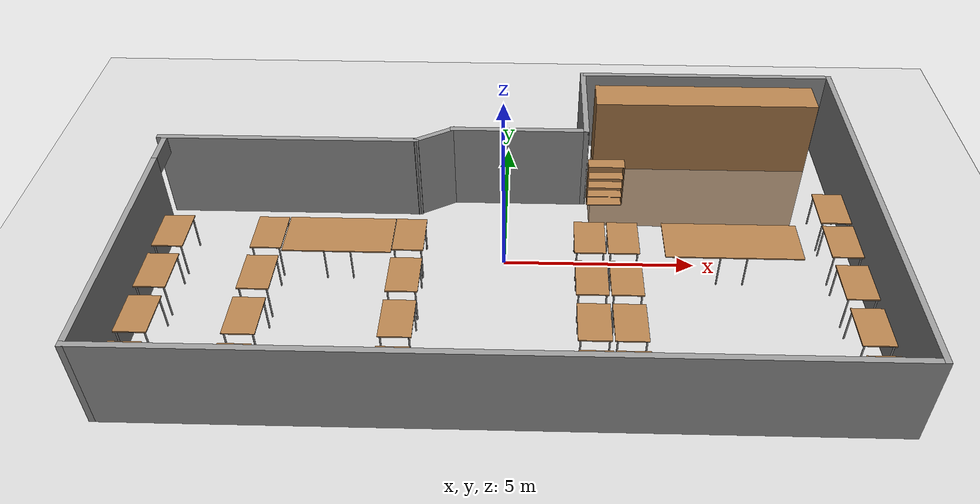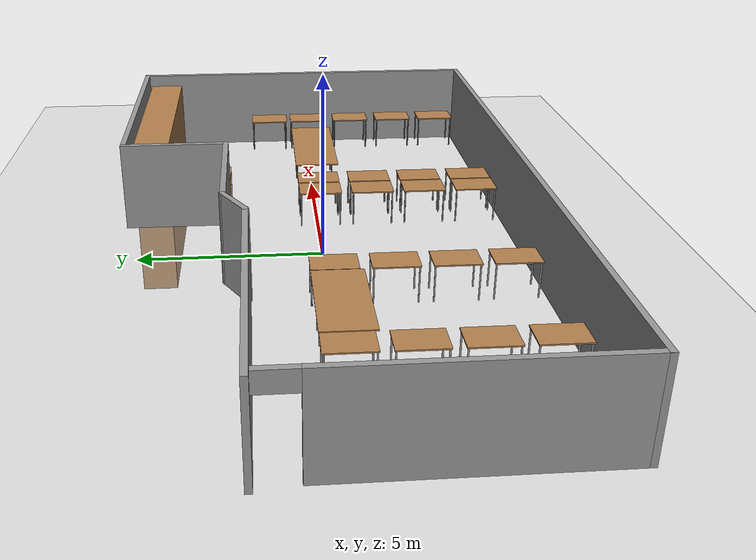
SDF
<sdf version="1.6">
 <world name="default">
  <light name="sun" type="directional">
   <pose>0 0 10 0 -0 0</pose>
   <diffuse>0.8 0.8 0.8 1</diffuse>
   <specular>0.1 0.1 0.1 1</specular>
   <attenuation>
    <range>1000</range>
    <constant>0.9</constant>
    <linear>0.01</linear>
    <quadratic>0.001</quadratic>
   </attenuation>
   <direction>-0.5 0.5 -1</direction>
  </light>
  <model name="ground_plane">
   <static>1</static>
   <link name="link">
    <collision name="collision">
     <geometry><plane><normal>0 0 1</normal><size>100 100</size></plane></geometry>
     <surface><friction><ode><mu>100</mu><mu2>50</mu2></ode></friction></surface>
    </collision>
    <visual name="visual">
     <cast_shadows>0</cast_shadows>
     <geometry><plane><normal>0 0 1</normal><size>100 100</size></plane></geometry>
     <material>
      <script><uri>file://media/materials/scripts/gazebo.material</uri><name>Gazebo/Grey</name></script>
     </material>
    </visual>
   </link>
  </model>
  <gravity>0 0 -9.8</gravity>
  <magnetic_field>6e-06 2.3e-05 -4.2e-05</magnetic_field>
  <atmosphere type="adiabatic"/>
  <physics name="default_physics" default="0" type="ode">
   <max_step_size>0.001</max_step_size>
   <real_time_factor>1</real_time_factor>
   <real_time_update_rate>1000</real_time_update_rate>
  </physics>
  <scene><ambient>0.4 0.4 0.4 1</ambient><background>0.7 0.7 0.7 1</background><shadows>1</shadows></scene>
  <spherical_coordinates>
   <surface_model>EARTH_WGS84</surface_model>
   <latitude_deg>0</latitude_deg>
   <longitude_deg>0</longitude_deg>
   <elevation>0</elevation>
   <heading_deg>0</heading_deg>
  </spherical_coordinates>
  <audio><device>default</device></audio>
  <model name="room_walls">
   <link name="Wall_0">
    <collision name="Wall_0_Collision">
     <geometry><box><size>7 0.15 2.5</size></box></geometry>
     <pose>0 0 1.25 0 -0 0</pose>
    </collision>
    <visual name="Wall_0_Visual">
     <pose>0 0 1.25 0 -0 0</pose>
     <geometry><box><size>7 0.15 2.5</size></box></geometry>
     <material>
      <script><uri>file://media/materials/scripts/gazebo.material</uri><name>Gazebo/Grey</name></script>
      <ambient>1 1 1 1</ambient>
     </material>
     <meta><layer>0</layer></meta>
    </visual>
    <pose>-5.82631 2.025 0 0 -0 0</pose>
   </link>
   <link name="Wall_1">
    <collision name="Wall_1_Collision">
     <geometry><box><size>1.25 0.15 2.5</size></box></geometry>
     <pose>0 0 1.25 0 -0 0</pose>
    </collision>
    <visual name="Wall_1_Visual">
     <pose>0 0 1.25 0 -0 0</pose>
     <geometry><box><size>1.25 0.15 2.5</size></box></geometry>
     <material>
      <script><uri>file://media/materials/scripts/gazebo.material</uri><name>Gazebo/Grey</name></script>
      <ambient>1 1 1 1</ambient>
     </material>
     <meta><layer>0</layer></meta>
    </visual>
    <pose>-1.925 2.3 0 0 -0 0.523599</pose>
   </link>
   <link name="Wall_2">
    <collision name="Wall_2_Collision">
     <geometry><box><size>3.75 0.15 2.5</size></box></geometry>
     <pose>0 0 1.25 0 -0 0</pose>
    </collision>
    <visual name="Wall_2_Visual">
     <pose>0 0 1.25 0 -0 0</pose>
     <geometry><box><size>3.75 0.15 2.5</size></box></geometry>
     <material>
      <script><uri>file://media/materials/scripts/gazebo.material</uri><name>Gazebo/Grey</name></script>
      <ambient>1 1 1 1</ambient>
     </material>
     <meta><layer>0</layer></meta>
    </visual>
    <pose>0.351314 2.575 0 0 -0 0</pose>
   </link>
   <link name="Wall_3">
    <collision name="Wall_3_Collision">
     <geometry><box><size>3 0.15 2.5</size></box></geometry>
     <pose>0 0 1.25 0 -0 0</pose>
    </collision>
    <visual name="Wall_3_Visual">
     <pose>0 0 1.25 0 -0 0</pose>
     <geometry><box><size>3 0.15 2.5</size></box></geometry>
     <material>
      <script><uri>file://media/materials/scripts/gazebo.material</uri><name>Gazebo/Grey</name></script>
      <ambient>1 1 1 1</ambient>
     </material>
     <meta><layer>0</layer></meta>
    </visual>
    <pose>2.15131 4 0 0 -0 1.5708</pose>
   </link>
   <link name="Wall_4">
    <collision name="Wall_4_Collision">
     <geometry><box><size>7.25 0.15 2.5</size></box></geometry>
     <pose>0 0 1.25 0 -0 0</pose>
    </collision>
    <visual name="Wall_4_Visual">
     <pose>0 0 1.25 0 -0 0</pose>
     <geometry><box><size>7.25 0.15 2.5</size></box></geometry>
     <material>
      <script><uri>file://media/materials/scripts/gazebo.material</uri><name>Gazebo/Grey</name></script>
      <ambient>1 1 1 1</ambient>
     </material>
     <meta><layer>0</layer></meta>
    </visual>
    <pose>5.70131 5.425 0 0 -0 0</pose>
   </link>
   <link name="Wall_5">
    <collision name="Wall_5_Collision">
     <geometry><box><size>11 0.15 2.5</size></box></geometry>
     <pose>0 0 1.25 0 -0 0</pose>
    </collision>
    <visual name="Wall_5_Visual">
     <pose>0 0 1.25 0 -0 0</pose>
     <geometry><box><size>11 0.15 2.5</size></box></geometry>
     <material>
      <script><uri>file://media/materials/scripts/gazebo.material</uri><name>Gazebo/Grey</name></script>
      <ambient>1 1 1 1</ambient>
     </material>
     <meta><layer>0</layer></meta>
    </visual>
    <pose>9.25131 0 0 0 -0 -1.5708</pose>
   </link>
   <link name="Wall_6">
    <collision name="Wall_6_Collision">
     <geometry><box><size>18.5 0.15 2.5</size></box></geometry>
     <pose>0 0 1.25 0 -0 0</pose>
    </collision>
    <visual name="Wall_6_Visual">
     <pose>0 0 1.25 0 -0 0</pose>
     <geometry><box><size>18.5 0.15 2.5</size></box></geometry>
     <material>
      <script><uri>file://media/materials/scripts/gazebo.material</uri><name>Gazebo/Grey</name></script>
      <ambient>1 1 1 1</ambient>
     </material>
     <meta><layer>0</layer></meta>
    </visual>
    <pose>0.076314 -5.425 0 0 -0 3.14159</pose>
   </link>
   <link name="Wall_7">
    <pose>-9.09869 -1.75 0 0 -0 1.5708</pose>
    <visual name="Wall_7_Visual_0">
     <pose>-0.476341 0 1.25 0 -0 0</pose>
     <geometry><box><size>6.54732 0.15 2.5</size></box></geometry>
     <material>
      <script><uri>file://media/materials/scripts/gazebo.material</uri><name>Gazebo/Grey</name></script>
      <ambient>1 1 1 1</ambient>
     </material>
     <meta><layer>0</layer></meta>
    </visual>
    <collision name="Wall_7_Collision_0">
     <geometry><box><size>6.54732 0.15 2.5</size></box></geometry>
     <pose>-0.476341 0 1.25 0 -0 0</pose>
    </collision>
    <visual name="Wall_7_Visual_2">
     <pose>3.24732 0 2.25 0 -0 0</pose>
     <geometry><box><size>0.9 0.15 0.5</size></box></geometry>
     <material>
      <script><uri>file://media/materials/scripts/gazebo.material</uri><name>Gazebo/Grey</name></script>
      <ambient>1 1 1 1</ambient>
     </material>
     <meta><layer>0</layer></meta>
    </visual>
    <collision name="Wall_7_Collision_2">
     <geometry><box><size>0.9 0.15 0.5</size></box></geometry>
     <pose>3.24732 0 2.25 0 -0 0</pose>
    </collision>
   </link>
   <static>1</static>
  </model>
  <model name="table_0">
   <pose>-8.6000628 -4.582113 0 0 -0 1.568221</pose>
   <static>1</static>
   <link name="table_0_link">
    <collision name="surface">
     <pose>0 0 1 0 -0 0</pose>
     <geometry><box><size>1.2 0.8 0.035</size></box></geometry>
     <surface><friction><ode><mu>0.6</mu><mu2>0.6</mu2></ode></friction></surface>
    </collision>
    <visual name="visual1">
     <pose>0 0 1 0 -0 0</pose>
     <geometry><box><size>1.2 0.8 0.035</size></box></geometry>
     <material>
      <script><uri>file://media/materials/scripts/gazebo.material</uri><name>Gazebo/Wood</name></script>
     </material>
    </visual>
    <collision name="front_left_leg">
     <pose>0.56 0.34 0.5 0 -0 0</pose>
     <geometry><cylinder><radius>0.02</radius><length>1</length></cylinder></geometry>
    </collision>
    <visual name="front_left_leg">
     <pose>0.56 0.34 0.5 0 -0 0</pose>
     <geometry><cylinder><radius>0.02</radius><length>1</length></cylinder></geometry>
     <material>
      <script><uri>file://media/materials/scripts/gazebo.material</uri><name>Gazebo/Grey</name></script>
     </material>
    </visual>
    <collision name="front_right_leg">
     <pose>0.56 -0.34 0.5 0 -0 0</pose>
     <geometry><cylinder><radius>0.02</radius><length>1</length></cylinder></geometry>
    </collision>
    <visual name="front_right_leg">
     <pose>0.56 -0.34 0.5 0 -0 0</pose>
     <geometry><cylinder><radius>0.02</radius><length>1</length></cylinder></geometry>
     <material>
      <script><uri>file://media/materials/scripts/gazebo.material</uri><name>Gazebo/Grey</name></script>
     </material>
    </visual>
    <collision name="back_right_leg">
     <pose>-0.56 -0.34 0.5 0 -0 0</pose>
     <geometry><cylinder><radius>0.02</radius><length>1</length></cylinder></geometry>
    </collision>
    <visual name="back_right_leg">
     <pose>-0.56 -0.34 0.5 0 -0 0</pose>
     <geometry><cylinder><radius>0.02</radius><length>1</length></cylinder></geometry>
     <material>
      <script><uri>file://media/materials/scripts/gazebo.material</uri><name>Gazebo/Grey</name></script>
     </material>
    </visual>
    <collision name="back_left_leg">
     <pose>-0.56 0.34 0.5 0 -0 0</pose>
     <geometry><cylinder><radius>0.02</radius><length>1</length></cylinder></geometry>
    </collision>
    <visual name="back_left_leg">
     <pose>-0.56 0.34 0.5 0 -0 0</pose>
     <geometry><cylinder><radius>0.02</radius><length>1</length></cylinder></geometry>
     <material>
      <script><uri>file://media/materials/scripts/gazebo.material</uri><name>Gazebo/Grey</name></script>
     </material>
    </visual>
   </link>
  </model>
  <model name="table_1">
   <pose>-8.6000628 -3.082113 0 0 -0 1.568221</pose>
   <static>1</static>
   <link name="table_1_link">
    <collision name="surface">
     <pose>0 0 1 0 -0 0</pose>
     <geometry><box><size>1.2 0.8 0.035</size></box></geometry>
     <surface><friction><ode><mu>0.6</mu><mu2>0.6</mu2></ode></friction></surface>
    </collision>
    <visual name="visual1">
     <pose>0 0 1 0 -0 0</pose>
     <geometry><box><size>1.2 0.8 0.035</size></box></geometry>
     <material>
      <script><uri>file://media/materials/scripts/gazebo.material</uri><name>Gazebo/Wood</name></script>
     </material>
    </visual>
    <collision name="front_left_leg">
     <pose>0.56 0.34 0.5 0 -0 0</pose>
     <geometry><cylinder><radius>0.02</radius><length>1</length></cylinder></geometry>
    </collision>
    <visual name="front_left_leg">
     <pose>0.56 0.34 0.5 0 -0 0</pose>
     <geometry><cylinder><radius>0.02</radius><length>1</length></cylinder></geometry>
     <material>
      <script><uri>file://media/materials/scripts/gazebo.material</uri><name>Gazebo/Grey</name></script>
     </material>
    </visual>
    <collision name="front_right_leg">
     <pose>0.56 -0.34 0.5 0 -0 0</pose>
     <geometry><cylinder><radius>0.02</radius><length>1</length></cylinder></geometry>
    </collision>
    <visual name="front_right_leg">
     <pose>0.56 -0.34 0.5 0 -0 0</pose>
     <geometry><cylinder><radius>0.02</radius><length>1</length></cylinder></geometry>
     <material>
      <script><uri>file://media/materials/scripts/gazebo.material</uri><name>Gazebo/Grey</name></script>
     </material>
    </visual>
    <collision name="back_right_leg">
     <pose>-0.56 -0.34 0.5 0 -0 0</pose>
     <geometry><cylinder><radius>0.02</radius><length>1</length></cylinder></geometry>
    </collision>
    <visual name="back_right_leg">
     <pose>-0.56 -0.34 0.5 0 -0 0</pose>
     <geometry><cylinder><radius>0.02</radius><length>1</length></cylinder></geometry>
     <material>
      <script><uri>file://media/materials/scripts/gazebo.material</uri><name>Gazebo/Grey</name></script>
     </material>
    </visual>
    <collision name="back_left_leg">
     <pose>-0.56 0.34 0.5 0 -0 0</pose>
     <geometry><cylinder><radius>0.02</radius><length>1</length></cylinder></geometry>
    </collision>
    <visual name="back_left_leg">
     <pose>-0.56 0.34 0.5 0 -0 0</pose>
     <geometry><cylinder><radius>0.02</radius><length>1</length></cylinder></geometry>
     <material>
      <script><uri>file://media/materials/scripts/gazebo.material</uri><name>Gazebo/Grey</name></script>
     </material>
    </visual>
   </link>
  </model>
  <model name="table_2">
   <pose>-8.6000628 -1.582113 0 0 -0 1.568221</pose>
   <static>1</static>
   <link name="table_2_link">
    <collision name="surface">
     <pose>0 0 1 0 -0 0</pose>
     <geometry><box><size>1.2 0.8 0.035</size></box></geometry>
     <surface><friction><ode><mu>0.6</mu><mu2>0.6</mu2></ode></friction></surface>
    </collision>
    <visual name="visual1">
     <pose>0 0 1 0 -0 0</pose>
     <geometry><box><size>1.2 0.8 0.035</size></box></geometry>
     <material>
      <script><uri>file://media/materials/scripts/gazebo.material</uri><name>Gazebo/Wood</name></script>
     </material>
    </visual>
    <collision name="front_left_leg">
     <pose>0.56 0.34 0.5 0 -0 0</pose>
     <geometry><cylinder><radius>0.02</radius><length>1</length></cylinder></geometry>
    </collision>
    <visual name="front_left_leg">
     <pose>0.56 0.34 0.5 0 -0 0</pose>
     <geometry><cylinder><radius>0.02</radius><length>1</length></cylinder></geometry>
     <material>
      <script><uri>file://media/materials/scripts/gazebo.material</uri><name>Gazebo/Grey</name></script>
     </material>
    </visual>
    <collision name="front_right_leg">
     <pose>0.56 -0.34 0.5 0 -0 0</pose>
     <geometry><cylinder><radius>0.02</radius><length>1</length></cylinder></geometry>
    </collision>
    <visual name="front_right_leg">
     <pose>0.56 -0.34 0.5 0 -0 0</pose>
     <geometry><cylinder><radius>0.02</radius><length>1</length></cylinder></geometry>
     <material>
      <script><uri>file://media/materials/scripts/gazebo.material</uri><name>Gazebo/Grey</name></script>
     </material>
    </visual>
    <collision name="back_right_leg">
     <pose>-0.56 -0.34 0.5 0 -0 0</pose>
     <geometry><cylinder><radius>0.02</radius><length>1</length></cylinder></geometry>
    </collision>
    <visual name="back_right_leg">
     <pose>-0.56 -0.34 0.5 0 -0 0</pose>
     <geometry><cylinder><radius>0.02</radius><length>1</length></cylinder></geometry>
     <material>
      <script><uri>file://media/materials/scripts/gazebo.material</uri><name>Gazebo/Grey</name></script>
     </material>
    </visual>
    <collision name="back_left_leg">
     <pose>-0.56 0.34 0.5 0 -0 0</pose>
     <geometry><cylinder><radius>0.02</radius><length>1</length></cylinder></geometry>
    </collision>
    <visual name="back_left_leg">
     <pose>-0.56 0.34 0.5 0 -0 0</pose>
     <geometry><cylinder><radius>0.02</radius><length>1</length></cylinder></geometry>
     <material>
      <script><uri>file://media/materials/scripts/gazebo.material</uri><name>Gazebo/Grey</name></script>
     </material>
    </visual>
   </link>
  </model>
  <model name="table_3">
   <pose>-8.6000628 -0.082113 0 0 -0 1.568221</pose>
   <static>1</static>
   <link name="table_3_link">
    <collision name="surface">
     <pose>0 0 1 0 -0 0</pose>
     <geometry><box><size>1.2 0.8 0.035</size></box></geometry>
     <surface><friction><ode><mu>0.6</mu><mu2>0.6</mu2></ode></friction></surface>
    </collision>
    <visual name="visual1">
     <pose>0 0 1 0 -0 0</pose>
     <geometry><box><size>1.2 0.8 0.035</size></box></geometry>
     <material>
      <script><uri>file://media/materials/scripts/gazebo.material</uri><name>Gazebo/Wood</name></script>
     </material>
    </visual>
    <collision name="front_left_leg">
     <pose>0.56 0.34 0.5 0 -0 0</pose>
     <geometry><cylinder><radius>0.02</radius><length>1</length></cylinder></geometry>
    </collision>
    <visual name="front_left_leg">
     <pose>0.56 0.34 0.5 0 -0 0</pose>
     <geometry><cylinder><radius>0.02</radius><length>1</length></cylinder></geometry>
     <material>
      <script><uri>file://media/materials/scripts/gazebo.material</uri><name>Gazebo/Grey</name></script>
     </material>
    </visual>
    <collision name="front_right_leg">
     <pose>0.56 -0.34 0.5 0 -0 0</pose>
     <geometry><cylinder><radius>0.02</radius><length>1</length></cylinder></geometry>
    </collision>
    <visual name="front_right_leg">
     <pose>0.56 -0.34 0.5 0 -0 0</pose>
     <geometry><cylinder><radius>0.02</radius><length>1</length></cylinder></geometry>
     <material>
      <script><uri>file://media/materials/scripts/gazebo.material</uri><name>Gazebo/Grey</name></script>
     </material>
    </visual>
    <collision name="back_right_leg">
     <pose>-0.56 -0.34 0.5 0 -0 0</pose>
     <geometry><cylinder><radius>0.02</radius><length>1</length></cylinder></geometry>
    </collision>
    <visual name="back_right_leg">
     <pose>-0.56 -0.34 0.5 0 -0 0</pose>
     <geometry><cylinder><radius>0.02</radius><length>1</length></cylinder></geometry>
     <material>
      <script><uri>file://media/materials/scripts/gazebo.material</uri><name>Gazebo/Grey</name></script>
     </material>
    </visual>
    <collision name="back_left_leg">
     <pose>-0.56 0.34 0.5 0 -0 0</pose>
     <geometry><cylinder><radius>0.02</radius><length>1</length></cylinder></geometry>
    </collision>
    <visual name="back_left_leg">
     <pose>-0.56 0.34 0.5 0 -0 0</pose>
     <geometry><cylinder><radius>0.02</radius><length>1</length></cylinder></geometry>
     <material>
      <script><uri>file://media/materials/scripts/gazebo.material</uri><name>Gazebo/Grey</name></script>
     </material>
    </visual>
   </link>
  </model>
  <model name="table_4">
   <pose>-6.070849 -4.582113 0 0 -0 1.568221</pose>
   <static>1</static>
   <link name="table_4_link">
    <collision name="surface">
     <pose>0 0 1 0 -0 0</pose>
     <geometry><box><size>1.2 0.8 0.035</size></box></geometry>
     <surface><friction><ode><mu>0.6</mu><mu2>0.6</mu2></ode></friction></surface>
    </collision>
    <visual name="visual1">
     <pose>0 0 1 0 -0 0</pose>
     <geometry><box><size>1.2 0.8 0.035</size></box></geometry>
     <material>
      <script><uri>file://media/materials/scripts/gazebo.material</uri><name>Gazebo/Wood</name></script>
     </material>
    </visual>
    <collision name="front_left_leg">
     <pose>0.56 0.34 0.5 0 -0 0</pose>
     <geometry><cylinder><radius>0.02</radius><length>1</length></cylinder></geometry>
    </collision>
    <visual name="front_left_leg">
     <pose>0.56 0.34 0.5 0 -0 0</pose>
     <geometry><cylinder><radius>0.02</radius><length>1</length></cylinder></geometry>
     <material>
      <script><uri>file://media/materials/scripts/gazebo.material</uri><name>Gazebo/Grey</name></script>
     </material>
    </visual>
    <collision name="front_right_leg">
     <pose>0.56 -0.34 0.5 0 -0 0</pose>
     <geometry><cylinder><radius>0.02</radius><length>1</length></cylinder></geometry>
    </collision>
    <visual name="front_right_leg">
     <pose>0.56 -0.34 0.5 0 -0 0</pose>
     <geometry><cylinder><radius>0.02</radius><length>1</length></cylinder></geometry>
     <material>
      <script><uri>file://media/materials/scripts/gazebo.material</uri><name>Gazebo/Grey</name></script>
     </material>
    </visual>
    <collision name="back_right_leg">
     <pose>-0.56 -0.34 0.5 0 -0 0</pose>
     <geometry><cylinder><radius>0.02</radius><length>1</length></cylinder></geometry>
    </collision>
    <visual name="back_right_leg">
     <pose>-0.56 -0.34 0.5 0 -0 0</pose>
     <geometry><cylinder><radius>0.02</radius><length>1</length></cylinder></geometry>
     <material>
      <script><uri>file://media/materials/scripts/gazebo.material</uri><name>Gazebo/Grey</name></script>
     </material>
    </visual>
    <collision name="back_left_leg">
     <pose>-0.56 0.34 0.5 0 -0 0</pose>
     <geometry><cylinder><radius>0.02</radius><length>1</length></cylinder></geometry>
    </collision>
    <visual name="back_left_leg">
     <pose>-0.56 0.34 0.5 0 -0 0</pose>
     <geometry><cylinder><radius>0.02</radius><length>1</length></cylinder></geometry>
     <material>
      <script><uri>file://media/materials/scripts/gazebo.material</uri><name>Gazebo/Grey</name></script>
     </material>
    </visual>
   </link>
  </model>
  <model name="table_5">
   <pose>-6.070849 -3.082113 0 0 -0 1.568221</pose>
   <static>1</static>
   <link name="table_5_link">
    <collision name="surface">
     <pose>0 0 1 0 -0 0</pose>
     <geometry><box><size>1.2 0.8 0.035</size></box></geometry>
     <surface><friction><ode><mu>0.6</mu><mu2>0.6</mu2></ode></friction></surface>
    </collision>
    <visual name="visual1">
     <pose>0 0 1 0 -0 0</pose>
     <geometry><box><size>1.2 0.8 0.035</size></box></geometry>
     <material>
      <script><uri>file://media/materials/scripts/gazebo.material</uri><name>Gazebo/Wood</name></script>
     </material>
    </visual>
    <collision name="front_left_leg">
     <pose>0.56 0.34 0.5 0 -0 0</pose>
     <geometry><cylinder><radius>0.02</radius><length>1</length></cylinder></geometry>
    </collision>
    <visual name="front_left_leg">
     <pose>0.56 0.34 0.5 0 -0 0</pose>
     <geometry><cylinder><radius>0.02</radius><length>1</length></cylinder></geometry>
     <material>
      <script><uri>file://media/materials/scripts/gazebo.material</uri><name>Gazebo/Grey</name></script>
     </material>
    </visual>
    <collision name="front_right_leg">
     <pose>0.56 -0.34 0.5 0 -0 0</pose>
     <geometry><cylinder><radius>0.02</radius><length>1</length></cylinder></geometry>
    </collision>
    <visual name="front_right_leg">
     <pose>0.56 -0.34 0.5 0 -0 0</pose>
     <geometry><cylinder><radius>0.02</radius><length>1</length></cylinder></geometry>
     <material>
      <script><uri>file://media/materials/scripts/gazebo.material</uri><name>Gazebo/Grey</name></script>
     </material>
    </visual>
    <collision name="back_right_leg">
     <pose>-0.56 -0.34 0.5 0 -0 0</pose>
     <geometry><cylinder><radius>0.02</radius><length>1</length></cylinder></geometry>
    </collision>
    <visual name="back_right_leg">
     <pose>-0.56 -0.34 0.5 0 -0 0</pose>
     <geometry><cylinder><radius>0.02</radius><length>1</length></cylinder></geometry>
     <material>
      <script><uri>file://media/materials/scripts/gazebo.material</uri><name>Gazebo/Grey</name></script>
     </material>
    </visual>
    <collision name="back_left_leg">
     <pose>-0.56 0.34 0.5 0 -0 0</pose>
     <geometry><cylinder><radius>0.02</radius><length>1</length></cylinder></geometry>
    </collision>
    <visual name="back_left_leg">
     <pose>-0.56 0.34 0.5 0 -0 0</pose>
     <geometry><cylinder><radius>0.02</radius><length>1</length></cylinder></geometry>
     <material>
      <script><uri>file://media/materials/scripts/gazebo.material</uri><name>Gazebo/Grey</name></script>
     </material>
    </visual>
   </link>
  </model>
  <model name="table_6">
   <pose>-6.070849 -1.582113 0 0 -0 1.568221</pose>
   <static>1</static>
   <link name="table_6_link">
    <collision name="surface">
     <pose>0 0 1 0 -0 0</pose>
     <geometry><box><size>1.2 0.8 0.035</size></box></geometry>
     <surface><friction><ode><mu>0.6</mu><mu2>0.6</mu2></ode></friction></surface>
    </collision>
    <visual name="visual1">
     <pose>0 0 1 0 -0 0</pose>
     <geometry><box><size>1.2 0.8 0.035</size></box></geometry>
     <material>
      <script><uri>file://media/materials/scripts/gazebo.material</uri><name>Gazebo/Wood</name></script>
     </material>
    </visual>
    <collision name="front_left_leg">
     <pose>0.56 0.34 0.5 0 -0 0</pose>
     <geometry><cylinder><radius>0.02</radius><length>1</length></cylinder></geometry>
    </collision>
    <visual name="front_left_leg">
     <pose>0.56 0.34 0.5 0 -0 0</pose>
     <geometry><cylinder><radius>0.02</radius><length>1</length></cylinder></geometry>
     <material>
      <script><uri>file://media/materials/scripts/gazebo.material</uri><name>Gazebo/Grey</name></script>
     </material>
    </visual>
    <collision name="front_right_leg">
     <pose>0.56 -0.34 0.5 0 -0 0</pose>
     <geometry><cylinder><radius>0.02</radius><length>1</length></cylinder></geometry>
    </collision>
    <visual name="front_right_leg">
     <pose>0.56 -0.34 0.5 0 -0 0</pose>
     <geometry><cylinder><radius>0.02</radius><length>1</length></cylinder></geometry>
     <material>
      <script><uri>file://media/materials/scripts/gazebo.material</uri><name>Gazebo/Grey</name></script>
     </material>
    </visual>
    <collision name="back_right_leg">
     <pose>-0.56 -0.34 0.5 0 -0 0</pose>
     <geometry><cylinder><radius>0.02</radius><length>1</length></cylinder></geometry>
    </collision>
    <visual name="back_right_leg">
     <pose>-0.56 -0.34 0.5 0 -0 0</pose>
     <geometry><cylinder><radius>0.02</radius><length>1</length></cylinder></geometry>
     <material>
      <script><uri>file://media/materials/scripts/gazebo.material</uri><name>Gazebo/Grey</name></script>
     </material>
    </visual>
    <collision name="back_left_leg">
     <pose>-0.56 0.34 0.5 0 -0 0</pose>
     <geometry><cylinder><radius>0.02</radius><length>1</length></cylinder></geometry>
    </collision>
    <visual name="back_left_leg">
     <pose>-0.56 0.34 0.5 0 -0 0</pose>
     <geometry><cylinder><radius>0.02</radius><length>1</length></cylinder></geometry>
     <material>
      <script><uri>file://media/materials/scripts/gazebo.material</uri><name>Gazebo/Grey</name></script>
     </material>
    </visual>
   </link>
  </model>
  <model name="table_7">
   <pose>-6.070849 -0.082113 0 0 -0 1.568221</pose>
   <static>1</static>
   <link name="table_7_link">
    <collision name="surface">
     <pose>0 0 1 0 -0 0</pose>
     <geometry><box><size>1.2 0.8 0.035</size></box></geometry>
     <surface><friction><ode><mu>0.6</mu><mu2>0.6</mu2></ode></friction></surface>
    </collision>
    <visual name="visual1">
     <pose>0 0 1 0 -0 0</pose>
     <geometry><box><size>1.2 0.8 0.035</size></box></geometry>
     <material>
      <script><uri>file://media/materials/scripts/gazebo.material</uri><name>Gazebo/Wood</name></script>
     </material>
    </visual>
    <collision name="front_left_leg">
     <pose>0.56 0.34 0.5 0 -0 0</pose>
     <geometry><cylinder><radius>0.02</radius><length>1</length></cylinder></geometry>
    </collision>
    <visual name="front_left_leg">
     <pose>0.56 0.34 0.5 0 -0 0</pose>
     <geometry><cylinder><radius>0.02</radius><length>1</length></cylinder></geometry>
     <material>
      <script><uri>file://media/materials/scripts/gazebo.material</uri><name>Gazebo/Grey</name></script>
     </material>
    </visual>
    <collision name="front_right_leg">
     <pose>0.56 -0.34 0.5 0 -0 0</pose>
     <geometry><cylinder><radius>0.02</radius><length>1</length></cylinder></geometry>
    </collision>
    <visual name="front_right_leg">
     <pose>0.56 -0.34 0.5 0 -0 0</pose>
     <geometry><cylinder><radius>0.02</radius><length>1</length></cylinder></geometry>
     <material>
      <script><uri>file://media/materials/scripts/gazebo.material</uri><name>Gazebo/Grey</name></script>
     </material>
    </visual>
    <collision name="back_right_leg">
     <pose>-0.56 -0.34 0.5 0 -0 0</pose>
     <geometry><cylinder><radius>0.02</radius><length>1</length></cylinder></geometry>
    </collision>
    <visual name="back_right_leg">
     <pose>-0.56 -0.34 0.5 0 -0 0</pose>
     <geometry><cylinder><radius>0.02</radius><length>1</length></cylinder></geometry>
     <material>
      <script><uri>file://media/materials/scripts/gazebo.material</uri><name>Gazebo/Grey</name></script>
     </material>
    </visual>
    <collision name="back_left_leg">
     <pose>-0.56 0.34 0.5 0 -0 0</pose>
     <geometry><cylinder><radius>0.02</radius><length>1</length></cylinder></geometry>
    </collision>
    <visual name="back_left_leg">
     <pose>-0.56 0.34 0.5 0 -0 0</pose>
     <geometry><cylinder><radius>0.02</radius><length>1</length></cylinder></geometry>
     <material>
      <script><uri>file://media/materials/scripts/gazebo.material</uri><name>Gazebo/Grey</name></script>
     </material>
    </visual>
   </link>
  </model>
  <model name="table_test_2">
   <pose>-4.242669 -0.129126 0  0 -0 1.568221</pose>
   <static>1</static>
   <link name="table_test_2_link">
    <collision name="surface">
     <pose>0 0 1 0 -0 0</pose>
     <geometry><box><size>1.3 2.78 0.035</size></box></geometry>
     <surface><friction><ode><mu>0.6</mu><mu2>0.6</mu2></ode></friction></surface>
    </collision>
    <visual name="visual1">
     <pose>0 0 1 0 -0 0</pose>
     <geometry><box><size>1.3 2.78 0.035</size></box></geometry>
     <material>
      <script><uri>file://media/materials/scripts/gazebo.material</uri><name>Gazebo/Wood</name></script>
     </material>
    </visual>
    <collision name="front_left_leg">
     <pose>0.56 0.34 0.5 0 -0 0</pose>
     <geometry><cylinder><radius>0.02</radius><length>1</length></cylinder></geometry>
    </collision>
    <visual name="front_left_leg">
     <pose>0.56 0.34 0.5 0 -0 0</pose>
     <geometry><cylinder><radius>0.02</radius><length>1</length></cylinder></geometry>
     <material>
      <script><uri>file://media/materials/scripts/gazebo.material</uri><name>Gazebo/Grey</name></script>
     </material>
    </visual>
    <collision name="front_right_leg">
     <pose>0.56 -0.34 0.5 0 -0 0</pose>
     <geometry><cylinder><radius>0.02</radius><length>1</length></cylinder></geometry>
    </collision>
    <visual name="front_right_leg">
     <pose>0.56 -0.34 0.5 0 -0 0</pose>
     <geometry><cylinder><radius>0.02</radius><length>1</length></cylinder></geometry>
     <material>
      <script><uri>file://media/materials/scripts/gazebo.material</uri><name>Gazebo/Grey</name></script>
     </material>
    </visual>
    <collision name="back_right_leg">
     <pose>-0.56 -0.34 0.5 0 -0 0</pose>
     <geometry><cylinder><radius>0.02</radius><length>1</length></cylinder></geometry>
    </collision>
    <visual name="back_right_leg">
     <pose>-0.56 -0.34 0.5 0 -0 0</pose>
     <geometry><cylinder><radius>0.02</radius><length>1</length></cylinder></geometry>
     <material>
      <script><uri>file://media/materials/scripts/gazebo.material</uri><name>Gazebo/Grey</name></script>
     </material>
    </visual>
    <collision name="back_left_leg">
     <pose>-0.56 0.34 0.5 0 -0 0</pose>
     <geometry><cylinder><radius>0.02</radius><length>1</length></cylinder></geometry>
    </collision>
    <visual name="back_left_leg">
     <pose>-0.56 0.34 0.5 0 -0 0</pose>
     <geometry><cylinder><radius>0.02</radius><length>1</length></cylinder></geometry>
     <material>
      <script><uri>file://media/materials/scripts/gazebo.material</uri><name>Gazebo/Grey</name></script>
     </material>
    </visual>
   </link>
  </model>
  <model name="table_8">
   <pose>-2.436673 -4.582113 0 0 -0 1.568221</pose>
   <static>1</static>
   <link name="table_8_link">
    <collision name="surface">
     <pose>0 0 1 0 -0 0</pose>
     <geometry><box><size>1.2 0.8 0.035</size></box></geometry>
     <surface><friction><ode><mu>0.6</mu><mu2>0.6</mu2></ode></friction></surface>
    </collision>
    <visual name="visual1">
     <pose>0 0 1 0 -0 0</pose>
     <geometry><box><size>1.2 0.8 0.035</size></box></geometry>
     <material>
      <script><uri>file://media/materials/scripts/gazebo.material</uri><name>Gazebo/Wood</name></script>
     </material>
    </visual>
    <collision name="front_left_leg">
     <pose>0.56 0.34 0.5 0 -0 0</pose>
     <geometry><cylinder><radius>0.02</radius><length>1</length></cylinder></geometry>
    </collision>
    <visual name="front_left_leg">
     <pose>0.56 0.34 0.5 0 -0 0</pose>
     <geometry><cylinder><radius>0.02</radius><length>1</length></cylinder></geometry>
     <material>
      <script><uri>file://media/materials/scripts/gazebo.material</uri><name>Gazebo/Grey</name></script>
     </material>
    </visual>
    <collision name="front_right_leg">
     <pose>0.56 -0.34 0.5 0 -0 0</pose>
     <geometry><cylinder><radius>0.02</radius><length>1</length></cylinder></geometry>
    </collision>
    <visual name="front_right_leg">
     <pose>0.56 -0.34 0.5 0 -0 0</pose>
     <geometry><cylinder><radius>0.02</radius><length>1</length></cylinder></geometry>
     <material>
      <script><uri>file://media/materials/scripts/gazebo.material</uri><name>Gazebo/Grey</name></script>
     </material>
    </visual>
    <collision name="back_right_leg">
     <pose>-0.56 -0.34 0.5 0 -0 0</pose>
     <geometry><cylinder><radius>0.02</radius><length>1</length></cylinder></geometry>
    </collision>
    <visual name="back_right_leg">
     <pose>-0.56 -0.34 0.5 0 -0 0</pose>
     <geometry><cylinder><radius>0.02</radius><length>1</length></cylinder></geometry>
     <material>
      <script><uri>file://media/materials/scripts/gazebo.material</uri><name>Gazebo/Grey</name></script>
     </material>
    </visual>
    <collision name="back_left_leg">
     <pose>-0.56 0.34 0.5 0 -0 0</pose>
     <geometry><cylinder><radius>0.02</radius><length>1</length></cylinder></geometry>
    </collision>
    <visual name="back_left_leg">
     <pose>-0.56 0.34 0.5 0 -0 0</pose>
     <geometry><cylinder><radius>0.02</radius><length>1</length></cylinder></geometry>
     <material>
      <script><uri>file://media/materials/scripts/gazebo.material</uri><name>Gazebo/Grey</name></script>
     </material>
    </visual>
   </link>
  </model>
  <model name="table_9">
   <pose>-2.436673 -3.082113 0 0 -0 1.568221</pose>
   <static>1</static>
   <link name="table_9_link">
    <collision name="surface">
     <pose>0 0 1 0 -0 0</pose>
     <geometry><box><size>1.2 0.8 0.035</size></box></geometry>
     <surface><friction><ode><mu>0.6</mu><mu2>0.6</mu2></ode></friction></surface>
    </collision>
    <visual name="visual1">
     <pose>0 0 1 0 -0 0</pose>
     <geometry><box><size>1.2 0.8 0.035</size></box></geometry>
     <material>
      <script><uri>file://media/materials/scripts/gazebo.material</uri><name>Gazebo/Wood</name></script>
     </material>
    </visual>
    <collision name="front_left_leg">
     <pose>0.56 0.34 0.5 0 -0 0</pose>
     <geometry><cylinder><radius>0.02</radius><length>1</length></cylinder></geometry>
    </collision>
    <visual name="front_left_leg">
     <pose>0.56 0.34 0.5 0 -0 0</pose>
     <geometry><cylinder><radius>0.02</radius><length>1</length></cylinder></geometry>
     <material>
      <script><uri>file://media/materials/scripts/gazebo.material</uri><name>Gazebo/Grey</name></script>
     </material>
    </visual>
    <collision name="front_right_leg">
     <pose>0.56 -0.34 0.5 0 -0 0</pose>
     <geometry><cylinder><radius>0.02</radius><length>1</length></cylinder></geometry>
    </collision>
    <visual name="front_right_leg">
     <pose>0.56 -0.34 0.5 0 -0 0</pose>
     <geometry><cylinder><radius>0.02</radius><length>1</length></cylinder></geometry>
     <material>
      <script><uri>file://media/materials/scripts/gazebo.material</uri><name>Gazebo/Grey</name></script>
     </material>
    </visual>
    <collision name="back_right_leg">
     <pose>-0.56 -0.34 0.5 0 -0 0</pose>
     <geometry><cylinder><radius>0.02</radius><length>1</length></cylinder></geometry>
    </collision>
    <visual name="back_right_leg">
     <pose>-0.56 -0.34 0.5 0 -0 0</pose>
     <geometry><cylinder><radius>0.02</radius><length>1</length></cylinder></geometry>
     <material>
      <script><uri>file://media/materials/scripts/gazebo.material</uri><name>Gazebo/Grey</name></script>
     </material>
    </visual>
    <collision name="back_left_leg">
     <pose>-0.56 0.34 0.5 0 -0 0</pose>
     <geometry><cylinder><radius>0.02</radius><length>1</length></cylinder></geometry>
    </collision>
    <visual name="back_left_leg">
     <pose>-0.56 0.34 0.5 0 -0 0</pose>
     <geometry><cylinder><radius>0.02</radius><length>1</length></cylinder></geometry>
     <material>
      <script><uri>file://media/materials/scripts/gazebo.material</uri><name>Gazebo/Grey</name></script>
     </material>
    </visual>
   </link>
  </model>
  <model name="table_10">
   <pose>-2.436673 -1.582113 0 0 -0 1.568221</pose>
   <static>1</static>
   <link name="table_10_link">
    <collision name="surface">
     <pose>0 0 1 0 -0 0</pose>
     <geometry><box><size>1.2 0.8 0.035</size></box></geometry>
     <surface><friction><ode><mu>0.6</mu><mu2>0.6</mu2></ode></friction></surface>
    </collision>
    <visual name="visual1">
     <pose>0 0 1 0 -0 0</pose>
     <geometry><box><size>1.2 0.8 0.035</size></box></geometry>
     <material>
      <script><uri>file://media/materials/scripts/gazebo.material</uri><name>Gazebo/Wood</name></script>
     </material>
    </visual>
    <collision name="front_left_leg">
     <pose>0.56 0.34 0.5 0 -0 0</pose>
     <geometry><cylinder><radius>0.02</radius><length>1</length></cylinder></geometry>
    </collision>
    <visual name="front_left_leg">
     <pose>0.56 0.34 0.5 0 -0 0</pose>
     <geometry><cylinder><radius>0.02</radius><length>1</length></cylinder></geometry>
     <material>
      <script><uri>file://media/materials/scripts/gazebo.material</uri><name>Gazebo/Grey</name></script>
     </material>
    </visual>
    <collision name="front_right_leg">
     <pose>0.56 -0.34 0.5 0 -0 0</pose>
     <geometry><cylinder><radius>0.02</radius><length>1</length></cylinder></geometry>
    </collision>
    <visual name="front_right_leg">
     <pose>0.56 -0.34 0.5 0 -0 0</pose>
     <geometry><cylinder><radius>0.02</radius><length>1</length></cylinder></geometry>
     <material>
      <script><uri>file://media/materials/scripts/gazebo.material</uri><name>Gazebo/Grey</name></script>
     </material>
    </visual>
    <collision name="back_right_leg">
     <pose>-0.56 -0.34 0.5 0 -0 0</pose>
     <geometry><cylinder><radius>0.02</radius><length>1</length></cylinder></geometry>
    </collision>
    <visual name="back_right_leg">
     <pose>-0.56 -0.34 0.5 0 -0 0</pose>
     <geometry><cylinder><radius>0.02</radius><length>1</length></cylinder></geometry>
     <material>
      <script><uri>file://media/materials/scripts/gazebo.material</uri><name>Gazebo/Grey</name></script>
     </material>
    </visual>
    <collision name="back_left_leg">
     <pose>-0.56 0.34 0.5 0 -0 0</pose>
     <geometry><cylinder><radius>0.02</radius><length>1</length></cylinder></geometry>
    </collision>
    <visual name="back_left_leg">
     <pose>-0.56 0.34 0.5 0 -0 0</pose>
     <geometry><cylinder><radius>0.02</radius><length>1</length></cylinder></geometry>
     <material>
      <script><uri>file://media/materials/scripts/gazebo.material</uri><name>Gazebo/Grey</name></script>
     </material>
    </visual>
   </link>
  </model>
  <model name="table_11">
   <pose>-2.436673 -0.082113 0 0 -0 1.568221</pose>
   <static>1</static>
   <link name="table_11_link">
    <collision name="surface">
     <pose>0 0 1 0 -0 0</pose>
     <geometry><box><size>1.2 0.8 0.035</size></box></geometry>
     <surface><friction><ode><mu>0.6</mu><mu2>0.6</mu2></ode></friction></surface>
    </collision>
    <visual name="visual1">
     <pose>0 0 1 0 -0 0</pose>
     <geometry><box><size>1.2 0.8 0.035</size></box></geometry>
     <material>
      <script><uri>file://media/materials/scripts/gazebo.material</uri><name>Gazebo/Wood</name></script>
     </material>
    </visual>
    <collision name="front_left_leg">
     <pose>0.56 0.34 0.5 0 -0 0</pose>
     <geometry><cylinder><radius>0.02</radius><length>1</length></cylinder></geometry>
    </collision>
    <visual name="front_left_leg">
     <pose>0.56 0.34 0.5 0 -0 0</pose>
     <geometry><cylinder><radius>0.02</radius><length>1</length></cylinder></geometry>
     <material>
      <script><uri>file://media/materials/scripts/gazebo.material</uri><name>Gazebo/Grey</name></script>
     </material>
    </visual>
    <collision name="front_right_leg">
     <pose>0.56 -0.34 0.5 0 -0 0</pose>
     <geometry><cylinder><radius>0.02</radius><length>1</length></cylinder></geometry>
    </collision>
    <visual name="front_right_leg">
     <pose>0.56 -0.34 0.5 0 -0 0</pose>
     <geometry><cylinder><radius>0.02</radius><length>1</length></cylinder></geometry>
     <material>
      <script><uri>file://media/materials/scripts/gazebo.material</uri><name>Gazebo/Grey</name></script>
     </material>
    </visual>
    <collision name="back_right_leg">
     <pose>-0.56 -0.34 0.5 0 -0 0</pose>
     <geometry><cylinder><radius>0.02</radius><length>1</length></cylinder></geometry>
    </collision>
    <visual name="back_right_leg">
     <pose>-0.56 -0.34 0.5 0 -0 0</pose>
     <geometry><cylinder><radius>0.02</radius><length>1</length></cylinder></geometry>
     <material>
      <script><uri>file://media/materials/scripts/gazebo.material</uri><name>Gazebo/Grey</name></script>
     </material>
    </visual>
    <collision name="back_left_leg">
     <pose>-0.56 0.34 0.5 0 -0 0</pose>
     <geometry><cylinder><radius>0.02</radius><length>1</length></cylinder></geometry>
    </collision>
    <visual name="back_left_leg">
     <pose>-0.56 0.34 0.5 0 -0 0</pose>
     <geometry><cylinder><radius>0.02</radius><length>1</length></cylinder></geometry>
     <material>
      <script><uri>file://media/materials/scripts/gazebo.material</uri><name>Gazebo/Grey</name></script>
     </material>
    </visual>
   </link>
  </model>
  <model name="table_12">
   <pose>2.211245 -4.582113 0 0 -0 1.568221</pose>
   <static>1</static>
   <link name="table_12_link">
    <collision name="surface">
     <pose>0 0 1 0 -0 0</pose>
     <geometry><box><size>1.2 0.8 0.035</size></box></geometry>
     <surface><friction><ode><mu>0.6</mu><mu2>0.6</mu2></ode></friction></surface>
    </collision>
    <visual name="visual1">
     <pose>0 0 1 0 -0 0</pose>
     <geometry><box><size>1.2 0.8 0.035</size></box></geometry>
     <material>
      <script><uri>file://media/materials/scripts/gazebo.material</uri><name>Gazebo/Wood</name></script>
     </material>
    </visual>
    <collision name="front_left_leg">
     <pose>0.56 0.34 0.5 0 -0 0</pose>
     <geometry><cylinder><radius>0.02</radius><length>1</length></cylinder></geometry>
    </collision>
    <visual name="front_left_leg">
     <pose>0.56 0.34 0.5 0 -0 0</pose>
     <geometry><cylinder><radius>0.02</radius><length>1</length></cylinder></geometry>
     <material>
      <script><uri>file://media/materials/scripts/gazebo.material</uri><name>Gazebo/Grey</name></script>
     </material>
    </visual>
    <collision name="front_right_leg">
     <pose>0.56 -0.34 0.5 0 -0 0</pose>
     <geometry><cylinder><radius>0.02</radius><length>1</length></cylinder></geometry>
    </collision>
    <visual name="front_right_leg">
     <pose>0.56 -0.34 0.5 0 -0 0</pose>
     <geometry><cylinder><radius>0.02</radius><length>1</length></cylinder></geometry>
     <material>
      <script><uri>file://media/materials/scripts/gazebo.material</uri><name>Gazebo/Grey</name></script>
     </material>
    </visual>
    <collision name="back_right_leg">
     <pose>-0.56 -0.34 0.5 0 -0 0</pose>
     <geometry><cylinder><radius>0.02</radius><length>1</length></cylinder></geometry>
    </collision>
    <visual name="back_right_leg">
     <pose>-0.56 -0.34 0.5 0 -0 0</pose>
     <geometry><cylinder><radius>0.02</radius><length>1</length></cylinder></geometry>
     <material>
      <script><uri>file://media/materials/scripts/gazebo.material</uri><name>Gazebo/Grey</name></script>
     </material>
    </visual>
    <collision name="back_left_leg">
     <pose>-0.56 0.34 0.5 0 -0 0</pose>
     <geometry><cylinder><radius>0.02</radius><length>1</length></cylinder></geometry>
    </collision>
    <visual name="back_left_leg">
     <pose>-0.56 0.34 0.5 0 -0 0</pose>
     <geometry><cylinder><radius>0.02</radius><length>1</length></cylinder></geometry>
     <material>
      <script><uri>file://media/materials/scripts/gazebo.material</uri><name>Gazebo/Grey</name></script>
     </material>
    </visual>
   </link>
  </model>
  <model name="table_13">
   <pose>2.211245 -3.082113 0 0 -0 1.568221</pose>
   <static>1</static>
   <link name="table_13_link">
    <collision name="surface">
     <pose>0 0 1 0 -0 0</pose>
     <geometry><box><size>1.2 0.8 0.035</size></box></geometry>
     <surface><friction><ode><mu>0.6</mu><mu2>0.6</mu2></ode></friction></surface>
    </collision>
    <visual name="visual1">
     <pose>0 0 1 0 -0 0</pose>
     <geometry><box><size>1.2 0.8 0.035</size></box></geometry>
     <material>
      <script><uri>file://media/materials/scripts/gazebo.material</uri><name>Gazebo/Wood</name></script>
     </material>
    </visual>
    <collision name="front_left_leg">
     <pose>0.56 0.34 0.5 0 -0 0</pose>
     <geometry><cylinder><radius>0.02</radius><length>1</length></cylinder></geometry>
    </collision>
    <visual name="front_left_leg">
     <pose>0.56 0.34 0.5 0 -0 0</pose>
     <geometry><cylinder><radius>0.02</radius><length>1</length></cylinder></geometry>
     <material>
      <script><uri>file://media/materials/scripts/gazebo.material</uri><name>Gazebo/Grey</name></script>
     </material>
    </visual>
    <collision name="front_right_leg">
     <pose>0.56 -0.34 0.5 0 -0 0</pose>
     <geometry><cylinder><radius>0.02</radius><length>1</length></cylinder></geometry>
    </collision>
    <visual name="front_right_leg">
     <pose>0.56 -0.34 0.5 0 -0 0</pose>
     <geometry><cylinder><radius>0.02</radius><length>1</length></cylinder></geometry>
     <material>
      <script><uri>file://media/materials/scripts/gazebo.material</uri><name>Gazebo/Grey</name></script>
     </material>
    </visual>
    <collision name="back_right_leg">
     <pose>-0.56 -0.34 0.5 0 -0 0</pose>
     <geometry><cylinder><radius>0.02</radius><length>1</length></cylinder></geometry>
    </collision>
    <visual name="back_right_leg">
     <pose>-0.56 -0.34 0.5 0 -0 0</pose>
     <geometry><cylinder><radius>0.02</radius><length>1</length></cylinder></geometry>
     <material>
      <script><uri>file://media/materials/scripts/gazebo.material</uri><name>Gazebo/Grey</name></script>
     </material>
    </visual>
    <collision name="back_left_leg">
     <pose>-0.56 0.34 0.5 0 -0 0</pose>
     <geometry><cylinder><radius>0.02</radius><length>1</length></cylinder></geometry>
    </collision>
    <visual name="back_left_leg">
     <pose>-0.56 0.34 0.5 0 -0 0</pose>
     <geometry><cylinder><radius>0.02</radius><length>1</length></cylinder></geometry>
     <material>
      <script><uri>file://media/materials/scripts/gazebo.material</uri><name>Gazebo/Grey</name></script>
     </material>
    </visual>
   </link>
  </model>
  <model name="table_14">
   <pose>2.211245 -1.582113 0 0 -0 1.568221</pose>
   <static>1</static>
   <link name="table_14_link">
    <collision name="surface">
     <pose>0 0 1 0 -0 0</pose>
     <geometry><box><size>1.2 0.8 0.035</size></box></geometry>
     <surface><friction><ode><mu>0.6</mu><mu2>0.6</mu2></ode></friction></surface>
    </collision>
    <visual name="visual1">
     <pose>0 0 1 0 -0 0</pose>
     <geometry><box><size>1.2 0.8 0.035</size></box></geometry>
     <material>
      <script><uri>file://media/materials/scripts/gazebo.material</uri><name>Gazebo/Wood</name></script>
     </material>
    </visual>
    <collision name="front_left_leg">
     <pose>0.56 0.34 0.5 0 -0 0</pose>
     <geometry><cylinder><radius>0.02</radius><length>1</length></cylinder></geometry>
    </collision>
    <visual name="front_left_leg">
     <pose>0.56 0.34 0.5 0 -0 0</pose>
     <geometry><cylinder><radius>0.02</radius><length>1</length></cylinder></geometry>
     <material>
      <script><uri>file://media/materials/scripts/gazebo.material</uri><name>Gazebo/Grey</name></script>
     </material>
    </visual>
    <collision name="front_right_leg">
     <pose>0.56 -0.34 0.5 0 -0 0</pose>
     <geometry><cylinder><radius>0.02</radius><length>1</length></cylinder></geometry>
    </collision>
    <visual name="front_right_leg">
     <pose>0.56 -0.34 0.5 0 -0 0</pose>
     <geometry><cylinder><radius>0.02</radius><length>1</length></cylinder></geometry>
     <material>
      <script><uri>file://media/materials/scripts/gazebo.material</uri><name>Gazebo/Grey</name></script>
     </material>
    </visual>
    <collision name="back_right_leg">
     <pose>-0.56 -0.34 0.5 0 -0 0</pose>
     <geometry><cylinder><radius>0.02</radius><length>1</length></cylinder></geometry>
    </collision>
    <visual name="back_right_leg">
     <pose>-0.56 -0.34 0.5 0 -0 0</pose>
     <geometry><cylinder><radius>0.02</radius><length>1</length></cylinder></geometry>
     <material>
      <script><uri>file://media/materials/scripts/gazebo.material</uri><name>Gazebo/Grey</name></script>
     </material>
    </visual>
    <collision name="back_left_leg">
     <pose>-0.56 0.34 0.5 0 -0 0</pose>
     <geometry><cylinder><radius>0.02</radius><length>1</length></cylinder></geometry>
    </collision>
    <visual name="back_left_leg">
     <pose>-0.56 0.34 0.5 0 -0 0</pose>
     <geometry><cylinder><radius>0.02</radius><length>1</length></cylinder></geometry>
     <material>
      <script><uri>file://media/materials/scripts/gazebo.material</uri><name>Gazebo/Grey</name></script>
     </material>
    </visual>
   </link>
  </model>
  <model name="table_15">
   <pose>2.211245 -0.082113 0 0 -0 1.568221</pose>
   <static>1</static>
   <link name="table_15_link">
    <collision name="surface">
     <pose>0 0 1 0 -0 0</pose>
     <geometry><box><size>1.2 0.8 0.035</size></box></geometry>
     <surface><friction><ode><mu>0.6</mu><mu2>0.6</mu2></ode></friction></surface>
    </collision>
    <visual name="visual1">
     <pose>0 0 1 0 -0 0</pose>
     <geometry><box><size>1.2 0.8 0.035</size></box></geometry>
     <material>
      <script><uri>file://media/materials/scripts/gazebo.material</uri><name>Gazebo/Wood</name></script>
     </material>
    </visual>
    <collision name="front_left_leg">
     <pose>0.56 0.34 0.5 0 -0 0</pose>
     <geometry><cylinder><radius>0.02</radius><length>1</length></cylinder></geometry>
    </collision>
    <visual name="front_left_leg">
     <pose>0.56 0.34 0.5 0 -0 0</pose>
     <geometry><cylinder><radius>0.02</radius><length>1</length></cylinder></geometry>
     <material>
      <script><uri>file://media/materials/scripts/gazebo.material</uri><name>Gazebo/Grey</name></script>
     </material>
    </visual>
    <collision name="front_right_leg">
     <pose>0.56 -0.34 0.5 0 -0 0</pose>
     <geometry><cylinder><radius>0.02</radius><length>1</length></cylinder></geometry>
    </collision>
    <visual name="front_right_leg">
     <pose>0.56 -0.34 0.5 0 -0 0</pose>
     <geometry><cylinder><radius>0.02</radius><length>1</length></cylinder></geometry>
     <material>
      <script><uri>file://media/materials/scripts/gazebo.material</uri><name>Gazebo/Grey</name></script>
     </material>
    </visual>
    <collision name="back_right_leg">
     <pose>-0.56 -0.34 0.5 0 -0 0</pose>
     <geometry><cylinder><radius>0.02</radius><length>1</length></cylinder></geometry>
    </collision>
    <visual name="back_right_leg">
     <pose>-0.56 -0.34 0.5 0 -0 0</pose>
     <geometry><cylinder><radius>0.02</radius><length>1</length></cylinder></geometry>
     <material>
      <script><uri>file://media/materials/scripts/gazebo.material</uri><name>Gazebo/Grey</name></script>
     </material>
    </visual>
    <collision name="back_left_leg">
     <pose>-0.56 0.34 0.5 0 -0 0</pose>
     <geometry><cylinder><radius>0.02</radius><length>1</length></cylinder></geometry>
    </collision>
    <visual name="back_left_leg">
     <pose>-0.56 0.34 0.5 0 -0 0</pose>
     <geometry><cylinder><radius>0.02</radius><length>1</length></cylinder></geometry>
     <material>
      <script><uri>file://media/materials/scripts/gazebo.material</uri><name>Gazebo/Grey</name></script>
     </material>
    </visual>
   </link>
  </model>
  <model name="table_16">
   <pose>3.069529 -4.582113 0 0 -0 1.568221</pose>
   <static>1</static>
   <link name="table_16_link">
    <collision name="surface">
     <pose>0 0 1 0 -0 0</pose>
     <geometry><box><size>1.2 0.8 0.035</size></box></geometry>
     <surface><friction><ode><mu>0.6</mu><mu2>0.6</mu2></ode></friction></surface>
    </collision>
    <visual name="visual1">
     <pose>0 0 1 0 -0 0</pose>
     <geometry><box><size>1.2 0.8 0.035</size></box></geometry>
     <material>
      <script><uri>file://media/materials/scripts/gazebo.material</uri><name>Gazebo/Wood</name></script>
     </material>
    </visual>
    <collision name="front_left_leg">
     <pose>0.56 0.34 0.5 0 -0 0</pose>
     <geometry><cylinder><radius>0.02</radius><length>1</length></cylinder></geometry>
    </collision>
    <visual name="front_left_leg">
     <pose>0.56 0.34 0.5 0 -0 0</pose>
     <geometry><cylinder><radius>0.02</radius><length>1</length></cylinder></geometry>
     <material>
      <script><uri>file://media/materials/scripts/gazebo.material</uri><name>Gazebo/Grey</name></script>
     </material>
    </visual>
    <collision name="front_right_leg">
     <pose>0.56 -0.34 0.5 0 -0 0</pose>
     <geometry><cylinder><radius>0.02</radius><length>1</length></cylinder></geometry>
    </collision>
    <visual name="front_right_leg">
     <pose>0.56 -0.34 0.5 0 -0 0</pose>
     <geometry><cylinder><radius>0.02</radius><length>1</length></cylinder></geometry>
     <material>
      <script><uri>file://media/materials/scripts/gazebo.material</uri><name>Gazebo/Grey</name></script>
     </material>
    </visual>
    <collision name="back_right_leg">
     <pose>-0.56 -0.34 0.5 0 -0 0</pose>
     <geometry><cylinder><radius>0.02</radius><length>1</length></cylinder></geometry>
    </collision>
    <visual name="back_right_leg">
     <pose>-0.56 -0.34 0.5 0 -0 0</pose>
     <geometry><cylinder><radius>0.02</radius><length>1</length></cylinder></geometry>
     <material>
      <script><uri>file://media/materials/scripts/gazebo.material</uri><name>Gazebo/Grey</name></script>
     </material>
    </visual>
    <collision name="back_left_leg">
     <pose>-0.56 0.34 0.5 0 -0 0</pose>
     <geometry><cylinder><radius>0.02</radius><length>1</length></cylinder></geometry>
    </collision>
    <visual name="back_left_leg">
     <pose>-0.56 0.34 0.5 0 -0 0</pose>
     <geometry><cylinder><radius>0.02</radius><length>1</length></cylinder></geometry>
     <material>
      <script><uri>file://media/materials/scripts/gazebo.material</uri><name>Gazebo/Grey</name></script>
     </material>
    </visual>
   </link>
  </model>
  <model name="table_17">
   <pose>3.069529 -3.082113 0 0 -0 1.568221</pose>
   <static>1</static>
   <link name="table_17_link">
    <collision name="surface">
     <pose>0 0 1 0 -0 0</pose>
     <geometry><box><size>1.2 0.8 0.035</size></box></geometry>
     <surface><friction><ode><mu>0.6</mu><mu2>0.6</mu2></ode></friction></surface>
    </collision>
    <visual name="visual1">
     <pose>0 0 1 0 -0 0</pose>
     <geometry><box><size>1.2 0.8 0.035</size></box></geometry>
     <material>
      <script><uri>file://media/materials/scripts/gazebo.material</uri><name>Gazebo/Wood</name></script>
     </material>
    </visual>
    <collision name="front_left_leg">
     <pose>0.56 0.34 0.5 0 -0 0</pose>
     <geometry><cylinder><radius>0.02</radius><length>1</length></cylinder></geometry>
    </collision>
    <visual name="front_left_leg">
     <pose>0.56 0.34 0.5 0 -0 0</pose>
     <geometry><cylinder><radius>0.02</radius><length>1</length></cylinder></geometry>
     <material>
      <script><uri>file://media/materials/scripts/gazebo.material</uri><name>Gazebo/Grey</name></script>
     </material>
    </visual>
    <collision name="front_right_leg">
     <pose>0.56 -0.34 0.5 0 -0 0</pose>
     <geometry><cylinder><radius>0.02</radius><length>1</length></cylinder></geometry>
    </collision>
    <visual name="front_right_leg">
     <pose>0.56 -0.34 0.5 0 -0 0</pose>
     <geometry><cylinder><radius>0.02</radius><length>1</length></cylinder></geometry>
     <material>
      <script><uri>file://media/materials/scripts/gazebo.material</uri><name>Gazebo/Grey</name></script>
     </material>
    </visual>
    <collision name="back_right_leg">
     <pose>-0.56 -0.34 0.5 0 -0 0</pose>
     <geometry><cylinder><radius>0.02</radius><length>1</length></cylinder></geometry>
    </collision>
    <visual name="back_right_leg">
     <pose>-0.56 -0.34 0.5 0 -0 0</pose>
     <geometry><cylinder><radius>0.02</radius><length>1</length></cylinder></geometry>
     <material>
      <script><uri>file://media/materials/scripts/gazebo.material</uri><name>Gazebo/Grey</name></script>
     </material>
    </visual>
    <collision name="back_left_leg">
     <pose>-0.56 0.34 0.5 0 -0 0</pose>
     <geometry><cylinder><radius>0.02</radius><length>1</length></cylinder></geometry>
    </collision>
    <visual name="back_left_leg">
     <pose>-0.56 0.34 0.5 0 -0 0</pose>
     <geometry><cylinder><radius>0.02</radius><length>1</length></cylinder></geometry>
     <material>
      <script><uri>file://media/materials/scripts/gazebo.material</uri><name>Gazebo/Grey</name></script>
     </material>
    </visual>
   </link>
  </model>
  <model name="table_18">
   <pose>3.069529 -1.582113 0 0 -0 1.568221</pose>
   <static>1</static>
   <link name="table_18_link">
    <collision name="surface">
     <pose>0 0 1 0 -0 0</pose>
     <geometry><box><size>1.2 0.8 0.035</size></box></geometry>
     <surface><friction><ode><mu>0.6</mu><mu2>0.6</mu2></ode></friction></surface>
    </collision>
    <visual name="visual1">
     <pose>0 0 1 0 -0 0</pose>
     <geometry><box><size>1.2 0.8 0.035</size></box></geometry>
     <material>
      <script><uri>file://media/materials/scripts/gazebo.material</uri><name>Gazebo/Wood</name></script>
     </material>
    </visual>
    <collision name="front_left_leg">
     <pose>0.56 0.34 0.5 0 -0 0</pose>
     <geometry><cylinder><radius>0.02</radius><length>1</length></cylinder></geometry>
    </collision>
    <visual name="front_left_leg">
     <pose>0.56 0.34 0.5 0 -0 0</pose>
     <geometry><cylinder><radius>0.02</radius><length>1</length></cylinder></geometry>
     <material>
      <script><uri>file://media/materials/scripts/gazebo.material</uri><name>Gazebo/Grey</name></script>
     </material>
    </visual>
    <collision name="front_right_leg">
     <pose>0.56 -0.34 0.5 0 -0 0</pose>
     <geometry><cylinder><radius>0.02</radius><length>1</length></cylinder></geometry>
    </collision>
    <visual name="front_right_leg">
     <pose>0.56 -0.34 0.5 0 -0 0</pose>
     <geometry><cylinder><radius>0.02</radius><length>1</length></cylinder></geometry>
     <material>
      <script><uri>file://media/materials/scripts/gazebo.material</uri><name>Gazebo/Grey</name></script>
     </material>
    </visual>
    <collision name="back_right_leg">
     <pose>-0.56 -0.34 0.5 0 -0 0</pose>
     <geometry><cylinder><radius>0.02</radius><length>1</length></cylinder></geometry>
    </collision>
    <visual name="back_right_leg">
     <pose>-0.56 -0.34 0.5 0 -0 0</pose>
     <geometry><cylinder><radius>0.02</radius><length>1</length></cylinder></geometry>
     <material>
      <script><uri>file://media/materials/scripts/gazebo.material</uri><name>Gazebo/Grey</name></script>
     </material>
    </visual>
    <collision name="back_left_leg">
     <pose>-0.56 0.34 0.5 0 -0 0</pose>
     <geometry><cylinder><radius>0.02</radius><length>1</length></cylinder></geometry>
    </collision>
    <visual name="back_left_leg">
     <pose>-0.56 0.34 0.5 0 -0 0</pose>
     <geometry><cylinder><radius>0.02</radius><length>1</length></cylinder></geometry>
     <material>
      <script><uri>file://media/materials/scripts/gazebo.material</uri><name>Gazebo/Grey</name></script>
     </material>
    </visual>
   </link>
  </model>
  <model name="table_19">
   <pose>3.069529 -0.082113 0 0 -0 1.568221</pose>
   <static>1</static>
   <link name="table_19_link">
    <collision name="surface">
     <pose>0 0 1 0 -0 0</pose>
     <geometry><box><size>1.2 0.8 0.035</size></box></geometry>
     <surface><friction><ode><mu>0.6</mu><mu2>0.6</mu2></ode></friction></surface>
    </collision>
    <visual name="visual1">
     <pose>0 0 1 0 -0 0</pose>
     <geometry><box><size>1.2 0.8 0.035</size></box></geometry>
     <material>
      <script><uri>file://media/materials/scripts/gazebo.material</uri><name>Gazebo/Wood</name></script>
     </material>
    </visual>
    <collision name="front_left_leg">
     <pose>0.56 0.34 0.5 0 -0 0</pose>
     <geometry><cylinder><radius>0.02</radius><length>1</length></cylinder></geometry>
    </collision>
    <visual name="front_left_leg">
     <pose>0.56 0.34 0.5 0 -0 0</pose>
     <geometry><cylinder><radius>0.02</radius><length>1</length></cylinder></geometry>
     <material>
      <script><uri>file://media/materials/scripts/gazebo.material</uri><name>Gazebo/Grey</name></script>
     </material>
    </visual>
    <collision name="front_right_leg">
     <pose>0.56 -0.34 0.5 0 -0 0</pose>
     <geometry><cylinder><radius>0.02</radius><length>1</length></cylinder></geometry>
    </collision>
    <visual name="front_right_leg">
     <pose>0.56 -0.34 0.5 0 -0 0</pose>
     <geometry><cylinder><radius>0.02</radius><length>1</length></cylinder></geometry>
     <material>
      <script><uri>file://media/materials/scripts/gazebo.material</uri><name>Gazebo/Grey</name></script>
     </material>
    </visual>
    <collision name="back_right_leg">
     <pose>-0.56 -0.34 0.5 0 -0 0</pose>
     <geometry><cylinder><radius>0.02</radius><length>1</length></cylinder></geometry>
    </collision>
    <visual name="back_right_leg">
     <pose>-0.56 -0.34 0.5 0 -0 0</pose>
     <geometry><cylinder><radius>0.02</radius><length>1</length></cylinder></geometry>
     <material>
      <script><uri>file://media/materials/scripts/gazebo.material</uri><name>Gazebo/Grey</name></script>
     </material>
    </visual>
    <collision name="back_left_leg">
     <pose>-0.56 0.34 0.5 0 -0 0</pose>
     <geometry><cylinder><radius>0.02</radius><length>1</length></cylinder></geometry>
    </collision>
    <visual name="back_left_leg">
     <pose>-0.56 0.34 0.5 0 -0 0</pose>
     <geometry><cylinder><radius>0.02</radius><length>1</length></cylinder></geometry>
     <material>
      <script><uri>file://media/materials/scripts/gazebo.material</uri><name>Gazebo/Grey</name></script>
     </material>
    </visual>
   </link>
  </model>
  <model name="table_20">
   <pose>5.852119 -0.129126 0  0 -0 1.568221</pose>
   <static>1</static>
   <link name="table_20_link">
    <collision name="surface">
     <pose>0 0 1 0 -0 0</pose>
     <geometry><box><size>1.3 3.50 0.035</size></box></geometry>
     <surface><friction><ode><mu>0.6</mu><mu2>0.6</mu2></ode></friction></surface>
    </collision>
    <visual name="visual1">
     <pose>0 0 1 0 -0 0</pose>
     <geometry><box><size>1.3 3.50 0.035</size></box></geometry>
     <material>
      <script><uri>file://media/materials/scripts/gazebo.material</uri><name>Gazebo/Wood</name></script>
     </material>
    </visual>
    <collision name="front_left_leg">
     <pose>0.56 0.34 0.5 0 -0 0</pose>
     <geometry><cylinder><radius>0.02</radius><length>1</length></cylinder></geometry>
    </collision>
    <visual name="front_left_leg">
     <pose>0.56 0.34 0.5 0 -0 0</pose>
     <geometry><cylinder><radius>0.02</radius><length>1</length></cylinder></geometry>
     <material>
      <script><uri>file://media/materials/scripts/gazebo.material</uri><name>Gazebo/Grey</name></script>
     </material>
    </visual>
    <collision name="front_right_leg">
     <pose>0.56 -0.34 0.5 0 -0 0</pose>
     <geometry><cylinder><radius>0.02</radius><length>1</length></cylinder></geometry>
    </collision>
    <visual name="front_right_leg">
     <pose>0.56 -0.34 0.5 0 -0 0</pose>
     <geometry><cylinder><radius>0.02</radius><length>1</length></cylinder></geometry>
     <material>
      <script><uri>file://media/materials/scripts/gazebo.material</uri><name>Gazebo/Grey</name></script>
     </material>
    </visual>
    <collision name="back_right_leg">
     <pose>-0.56 -0.34 0.5 0 -0 0</pose>
     <geometry><cylinder><radius>0.02</radius><length>1</length></cylinder></geometry>
    </collision>
    <visual name="back_right_leg">
     <pose>-0.56 -0.34 0.5 0 -0 0</pose>
     <geometry><cylinder><radius>0.02</radius><length>1</length></cylinder></geometry>
     <material>
      <script><uri>file://media/materials/scripts/gazebo.material</uri><name>Gazebo/Grey</name></script>
     </material>
    </visual>
    <collision name="back_left_leg">
     <pose>-0.56 0.34 0.5 0 -0 0</pose>
     <geometry><cylinder><radius>0.02</radius><length>1</length></cylinder></geometry>
    </collision>
    <visual name="back_left_leg">
     <pose>-0.56 0.34 0.5 0 -0 0</pose>
     <geometry><cylinder><radius>0.02</radius><length>1</length></cylinder></geometry>
     <material>
      <script><uri>file://media/materials/scripts/gazebo.material</uri><name>Gazebo/Grey</name></script>
     </material>
    </visual>
   </link>
  </model>
  <model name="table_120">
   <pose>8.713411 -4.582113 0 0 -0 1.568221</pose>
   <static>1</static>
   <link name="table_120_link">
    <collision name="surface">
     <pose>0 0 1 0 -0 0</pose>
     <geometry><box><size>1.2 0.8 0.035</size></box></geometry>
     <surface><friction><ode><mu>0.6</mu><mu2>0.6</mu2></ode></friction></surface>
    </collision>
    <visual name="visual1">
     <pose>0 0 1 0 -0 0</pose>
     <geometry><box><size>1.2 0.8 0.035</size></box></geometry>
     <material>
      <script><uri>file://media/materials/scripts/gazebo.material</uri><name>Gazebo/Wood</name></script>
     </material>
    </visual>
    <collision name="front_left_leg">
     <pose>0.56 0.34 0.5 0 -0 0</pose>
     <geometry><cylinder><radius>0.02</radius><length>1</length></cylinder></geometry>
    </collision>
    <visual name="front_left_leg">
     <pose>0.56 0.34 0.5 0 -0 0</pose>
     <geometry><cylinder><radius>0.02</radius><length>1</length></cylinder></geometry>
     <material>
      <script><uri>file://media/materials/scripts/gazebo.material</uri><name>Gazebo/Grey</name></script>
     </material>
    </visual>
    <collision name="front_right_leg">
     <pose>0.56 -0.34 0.5 0 -0 0</pose>
     <geometry><cylinder><radius>0.02</radius><length>1</length></cylinder></geometry>
    </collision>
    <visual name="front_right_leg">
     <pose>0.56 -0.34 0.5 0 -0 0</pose>
     <geometry><cylinder><radius>0.02</radius><length>1</length></cylinder></geometry>
     <material>
      <script><uri>file://media/materials/scripts/gazebo.material</uri><name>Gazebo/Grey</name></script>
     </material>
    </visual>
    <collision name="back_right_leg">
     <pose>-0.56 -0.34 0.5 0 -0 0</pose>
     <geometry><cylinder><radius>0.02</radius><length>1</length></cylinder></geometry>
    </collision>
    <visual name="back_right_leg">
     <pose>-0.56 -0.34 0.5 0 -0 0</pose>
     <geometry><cylinder><radius>0.02</radius><length>1</length></cylinder></geometry>
     <material>
      <script><uri>file://media/materials/scripts/gazebo.material</uri><name>Gazebo/Grey</name></script>
     </material>
    </visual>
    <collision name="back_left_leg">
     <pose>-0.56 0.34 0.5 0 -0 0</pose>
     <geometry><cylinder><radius>0.02</radius><length>1</length></cylinder></geometry>
    </collision>
    <visual name="back_left_leg">
     <pose>-0.56 0.34 0.5 0 -0 0</pose>
     <geometry><cylinder><radius>0.02</radius><length>1</length></cylinder></geometry>
     <material>
      <script><uri>file://media/materials/scripts/gazebo.material</uri><name>Gazebo/Grey</name></script>
     </material>
    </visual>
   </link>
  </model>
  <model name="table_121">
   <pose>8.713411 -3.082113 0 0 -0 1.568221</pose>
   <static>1</static>
   <link name="table_121_link">
    <collision name="surface">
     <pose>0 0 1 0 -0 0</pose>
     <geometry><box><size>1.2 0.8 0.035</size></box></geometry>
     <surface><friction><ode><mu>0.6</mu><mu2>0.6</mu2></ode></friction></surface>
    </collision>
    <visual name="visual1">
     <pose>0 0 1 0 -0 0</pose>
     <geometry><box><size>1.2 0.8 0.035</size></box></geometry>
     <material>
      <script><uri>file://media/materials/scripts/gazebo.material</uri><name>Gazebo/Wood</name></script>
     </material>
    </visual>
    <collision name="front_left_leg">
     <pose>0.56 0.34 0.5 0 -0 0</pose>
     <geometry><cylinder><radius>0.02</radius><length>1</length></cylinder></geometry>
    </collision>
    <visual name="front_left_leg">
     <pose>0.56 0.34 0.5 0 -0 0</pose>
     <geometry><cylinder><radius>0.02</radius><length>1</length></cylinder></geometry>
     <material>
      <script><uri>file://media/materials/scripts/gazebo.material</uri><name>Gazebo/Grey</name></script>
     </material>
    </visual>
    <collision name="front_right_leg">
     <pose>0.56 -0.34 0.5 0 -0 0</pose>
     <geometry><cylinder><radius>0.02</radius><length>1</length></cylinder></geometry>
    </collision>
    <visual name="front_right_leg">
     <pose>0.56 -0.34 0.5 0 -0 0</pose>
     <geometry><cylinder><radius>0.02</radius><length>1</length></cylinder></geometry>
     <material>
      <script><uri>file://media/materials/scripts/gazebo.material</uri><name>Gazebo/Grey</name></script>
     </material>
    </visual>
    <collision name="back_right_leg">
     <pose>-0.56 -0.34 0.5 0 -0 0</pose>
     <geometry><cylinder><radius>0.02</radius><length>1</length></cylinder></geometry>
    </collision>
    <visual name="back_right_leg">
     <pose>-0.56 -0.34 0.5 0 -0 0</pose>
     <geometry><cylinder><radius>0.02</radius><length>1</length></cylinder></geometry>
     <material>
      <script><uri>file://media/materials/scripts/gazebo.material</uri><name>Gazebo/Grey</name></script>
     </material>
    </visual>
    <collision name="back_left_leg">
     <pose>-0.56 0.34 0.5 0 -0 0</pose>
     <geometry><cylinder><radius>0.02</radius><length>1</length></cylinder></geometry>
    </collision>
    <visual name="back_left_leg">
     <pose>-0.56 0.34 0.5 0 -0 0</pose>
     <geometry><cylinder><radius>0.02</radius><length>1</length></cylinder></geometry>
     <material>
      <script><uri>file://media/materials/scripts/gazebo.material</uri><name>Gazebo/Grey</name></script>
     </material>
    </visual>
   </link>
  </model>
  <model name="table_122">
   <pose>8.713411 -1.582113 0 0 -0 1.568221</pose>
   <static>1</static>
   <link name="table_122_link">
    <collision name="surface">
     <pose>0 0 1 0 -0 0</pose>
     <geometry><box><size>1.2 0.8 0.035</size></box></geometry>
     <surface><friction><ode><mu>0.6</mu><mu2>0.6</mu2></ode></friction></surface>
    </collision>
    <visual name="visual1">
     <pose>0 0 1 0 -0 0</pose>
     <geometry><box><size>1.2 0.8 0.035</size></box></geometry>
     <material>
      <script><uri>file://media/materials/scripts/gazebo.material</uri><name>Gazebo/Wood</name></script>
     </material>
    </visual>
    <collision name="front_left_leg">
     <pose>0.56 0.34 0.5 0 -0 0</pose>
     <geometry><cylinder><radius>0.02</radius><length>1</length></cylinder></geometry>
    </collision>
    <visual name="front_left_leg">
     <pose>0.56 0.34 0.5 0 -0 0</pose>
     <geometry><cylinder><radius>0.02</radius><length>1</length></cylinder></geometry>
     <material>
      <script><uri>file://media/materials/scripts/gazebo.material</uri><name>Gazebo/Grey</name></script>
     </material>
    </visual>
    <collision name="front_right_leg">
     <pose>0.56 -0.34 0.5 0 -0 0</pose>
     <geometry><cylinder><radius>0.02</radius><length>1</length></cylinder></geometry>
    </collision>
    <visual name="front_right_leg">
     <pose>0.56 -0.34 0.5 0 -0 0</pose>
     <geometry><cylinder><radius>0.02</radius><length>1</length></cylinder></geometry>
     <material>
      <script><uri>file://media/materials/scripts/gazebo.material</uri><name>Gazebo/Grey</name></script>
     </material>
    </visual>
    <collision name="back_right_leg">
     <pose>-0.56 -0.34 0.5 0 -0 0</pose>
     <geometry><cylinder><radius>0.02</radius><length>1</length></cylinder></geometry>
    </collision>
    <visual name="back_right_leg">
     <pose>-0.56 -0.34 0.5 0 -0 0</pose>
     <geometry><cylinder><radius>0.02</radius><length>1</length></cylinder></geometry>
     <material>
      <script><uri>file://media/materials/scripts/gazebo.material</uri><name>Gazebo/Grey</name></script>
     </material>
    </visual>
    <collision name="back_left_leg">
     <pose>-0.56 0.34 0.5 0 -0 0</pose>
     <geometry><cylinder><radius>0.02</radius><length>1</length></cylinder></geometry>
    </collision>
    <visual name="back_left_leg">
     <pose>-0.56 0.34 0.5 0 -0 0</pose>
     <geometry><cylinder><radius>0.02</radius><length>1</length></cylinder></geometry>
     <material>
      <script><uri>file://media/materials/scripts/gazebo.material</uri><name>Gazebo/Grey</name></script>
     </material>
    </visual>
   </link>
  </model>
  <model name="table_123">
   <pose>8.713411 -0.082113 0 0 -0 1.568221</pose>
   <static>1</static>
   <link name="table_123_link">
    <collision name="surface">
     <pose>0 0 1 0 -0 0</pose>
     <geometry><box><size>1.2 0.8 0.035</size></box></geometry>
     <surface><friction><ode><mu>0.6</mu><mu2>0.6</mu2></ode></friction></surface>
    </collision>
    <visual name="visual1">
     <pose>0 0 1 0 -0 0</pose>
     <geometry><box><size>1.2 0.8 0.035</size></box></geometry>
     <material>
      <script><uri>file://media/materials/scripts/gazebo.material</uri><name>Gazebo/Wood</name></script>
     </material>
    </visual>
    <collision name="front_left_leg">
     <pose>0.56 0.34 0.5 0 -0 0</pose>
     <geometry><cylinder><radius>0.02</radius><length>1</length></cylinder></geometry>
    </collision>
    <visual name="front_left_leg">
     <pose>0.56 0.34 0.5 0 -0 0</pose>
     <geometry><cylinder><radius>0.02</radius><length>1</length></cylinder></geometry>
     <material>
      <script><uri>file://media/materials/scripts/gazebo.material</uri><name>Gazebo/Grey</name></script>
     </material>
    </visual>
    <collision name="front_right_leg">
     <pose>0.56 -0.34 0.5 0 -0 0</pose>
     <geometry><cylinder><radius>0.02</radius><length>1</length></cylinder></geometry>
    </collision>
    <visual name="front_right_leg">
     <pose>0.56 -0.34 0.5 0 -0 0</pose>
     <geometry><cylinder><radius>0.02</radius><length>1</length></cylinder></geometry>
     <material>
      <script><uri>file://media/materials/scripts/gazebo.material</uri><name>Gazebo/Grey</name></script>
     </material>
    </visual>
    <collision name="back_right_leg">
     <pose>-0.56 -0.34 0.5 0 -0 0</pose>
     <geometry><cylinder><radius>0.02</radius><length>1</length></cylinder></geometry>
    </collision>
    <visual name="back_right_leg">
     <pose>-0.56 -0.34 0.5 0 -0 0</pose>
     <geometry><cylinder><radius>0.02</radius><length>1</length></cylinder></geometry>
     <material>
      <script><uri>file://media/materials/scripts/gazebo.material</uri><name>Gazebo/Grey</name></script>
     </material>
    </visual>
    <collision name="back_left_leg">
     <pose>-0.56 0.34 0.5 0 -0 0</pose>
     <geometry><cylinder><radius>0.02</radius><length>1</length></cylinder></geometry>
    </collision>
    <visual name="back_left_leg">
     <pose>-0.56 0.34 0.5 0 -0 0</pose>
     <geometry><cylinder><radius>0.02</radius><length>1</length></cylinder></geometry>
     <material>
      <script><uri>file://media/materials/scripts/gazebo.material</uri><name>Gazebo/Grey</name></script>
     </material>
    </visual>
   </link>
  </model>
  <model name="table_124">
   <pose>8.713411 1.244753 0  0 -0 1.568221</pose>
   <static>1</static>
   <link name="table_124_link">
    <collision name="surface">
     <pose>0 0 1 0 -0 0</pose>
     <geometry><box><size>1.2 0.8 0.035</size></box></geometry>
     <surface><friction><ode><mu>0.6</mu><mu2>0.6</mu2></ode></friction></surface>
    </collision>
    <visual name="visual1">
     <pose>0 0 1 0 -0 0</pose>
     <geometry><box><size>1.2 0.8 0.035</size></box></geometry>
     <material>
      <script><uri>file://media/materials/scripts/gazebo.material</uri><name>Gazebo/Wood</name></script>
     </material>
    </visual>
    <collision name="front_left_leg">
     <pose>0.56 0.34 0.5 0 -0 0</pose>
     <geometry><cylinder><radius>0.02</radius><length>1</length></cylinder></geometry>
    </collision>
    <visual name="front_left_leg">
     <pose>0.56 0.34 0.5 0 -0 0</pose>
     <geometry><cylinder><radius>0.02</radius><length>1</length></cylinder></geometry>
     <material>
      <script><uri>file://media/materials/scripts/gazebo.material</uri><name>Gazebo/Grey</name></script>
     </material>
    </visual>
    <collision name="front_right_leg">
     <pose>0.56 -0.34 0.5 0 -0 0</pose>
     <geometry><cylinder><radius>0.02</radius><length>1</length></cylinder></geometry>
    </collision>
    <visual name="front_right_leg">
     <pose>0.56 -0.34 0.5 0 -0 0</pose>
     <geometry><cylinder><radius>0.02</radius><length>1</length></cylinder></geometry>
     <material>
      <script><uri>file://media/materials/scripts/gazebo.material</uri><name>Gazebo/Grey</name></script>
     </material>
    </visual>
    <collision name="back_right_leg">
     <pose>-0.56 -0.34 0.5 0 -0 0</pose>
     <geometry><cylinder><radius>0.02</radius><length>1</length></cylinder></geometry>
    </collision>
    <visual name="back_right_leg">
     <pose>-0.56 -0.34 0.5 0 -0 0</pose>
     <geometry><cylinder><radius>0.02</radius><length>1</length></cylinder></geometry>
     <material>
      <script><uri>file://media/materials/scripts/gazebo.material</uri><name>Gazebo/Grey</name></script>
     </material>
    </visual>
    <collision name="back_left_leg">
     <pose>-0.56 0.34 0.5 0 -0 0</pose>
     <geometry><cylinder><radius>0.02</radius><length>1</length></cylinder></geometry>
    </collision>
    <visual name="back_left_leg">
     <pose>-0.56 0.34 0.5 0 -0 0</pose>
     <geometry><cylinder><radius>0.02</radius><length>1</length></cylinder></geometry>
     <material>
      <script><uri>file://media/materials/scripts/gazebo.material</uri><name>Gazebo/Grey</name></script>
     </material>
    </visual>
   </link>
  </model>
  <model name="ias_lab_bookshelf_0">
   <pose>2.770291 2.662647 0  0 0 -1.5707963</pose>
   <static>true</static>
   <link name="ias_lab_bookshelf_0_link">
    <inertial><mass>100</mass></inertial>
    <visual name="visual">
     <geometry>
      <mesh><uri>model://wheelchair_iaslab_gazebo/meshes/bookshelf.dae</uri><scale>1 1 1</scale></mesh>
     </geometry>
     <material>
      <script><name>Gazebo/Wood</name><uri>file://media/materials/scripts/gazebo.material</uri></script>
     </material>
    </visual>
    <collision name="collision">
     <geometry>
      <mesh><uri>model://wheelchair_iaslab_gazebo/meshes/bookshelf.dae</uri><scale>1 1 1</scale></mesh>
     </geometry>
    </collision>
   </link>
  </model>
  <model name="bookshelfs">
   <pose>5.648703 4.731802 0  0 -0.001854 0.000194</pose>
   <link name="bookshelfs_link">
    <inertial>
     <mass>1.93435</mass>
     <inertia>
      <ixx>0.322392</ixx>
      <ixy>0</ixy>
      <ixz>0</ixz>
      <iyy>0.764337</iyy>
      <iyz>0</iyz>
      <izz>0.764337</izz>
     </inertia>
    </inertial>
    <pose>-1e-06 -1e-06 0 0 -0 0</pose>
    <visual name="visual">
     <geometry><box><size>6.256060 1 4.5</size></box></geometry>
     <material>
      <lighting>1</lighting>
      <script><uri>file://media/materials/scripts/gazebo.material</uri><name>Gazebo/Wood</name></script>
     </material>
    </visual>
    <collision name="collision">
     <geometry><box><size>6.256060 1 4.5</size></box></geometry>
     <surface>
      <friction>
       <ode><mu>1</mu><mu2>1</mu2><fdir1>0 0 0</fdir1><slip1>0</slip1><slip2>0</slip2></ode>
       <torsional>
        <coefficient>1</coefficient>
        <patch_radius>0</patch_radius>
        <surface_radius>0</surface_radius>
        <use_patch_radius>1</use_patch_radius>
        <ode><slip>0</slip></ode>
       </torsional>
      </friction>
      <bounce><restitution_coefficient>0</restitution_coefficient><threshold>1e+06</threshold></bounce>
      <contact>
       <collide_without_contact>0</collide_without_contact>
       <collide_without_contact_bitmask>1</collide_without_contact_bitmask>
       <collide_bitmask>1</collide_bitmask>
       <ode>
        <soft_cfm>0</soft_cfm>
        <soft_erp>0.2</soft_erp>
        <kp>1e+13</kp>
        <kd>1</kd>
        <max_vel>0.01</max_vel>
        <min_depth>0</min_depth>
       </ode>
       <bullet>
        <split_impulse>1</split_impulse>
        <split_impulse_penetration_threshold>-0.01</split_impulse_penetration_threshold>
        <soft_cfm>0</soft_cfm>
        <soft_erp>0.2</soft_erp>
        <kp>1e+13</kp>
        <kd>1</kd>
       </bullet>
      </contact>
     </surface>
    </collision>
   </link>
   <static>true</static>
  </model>
 </world>
</sdf>
